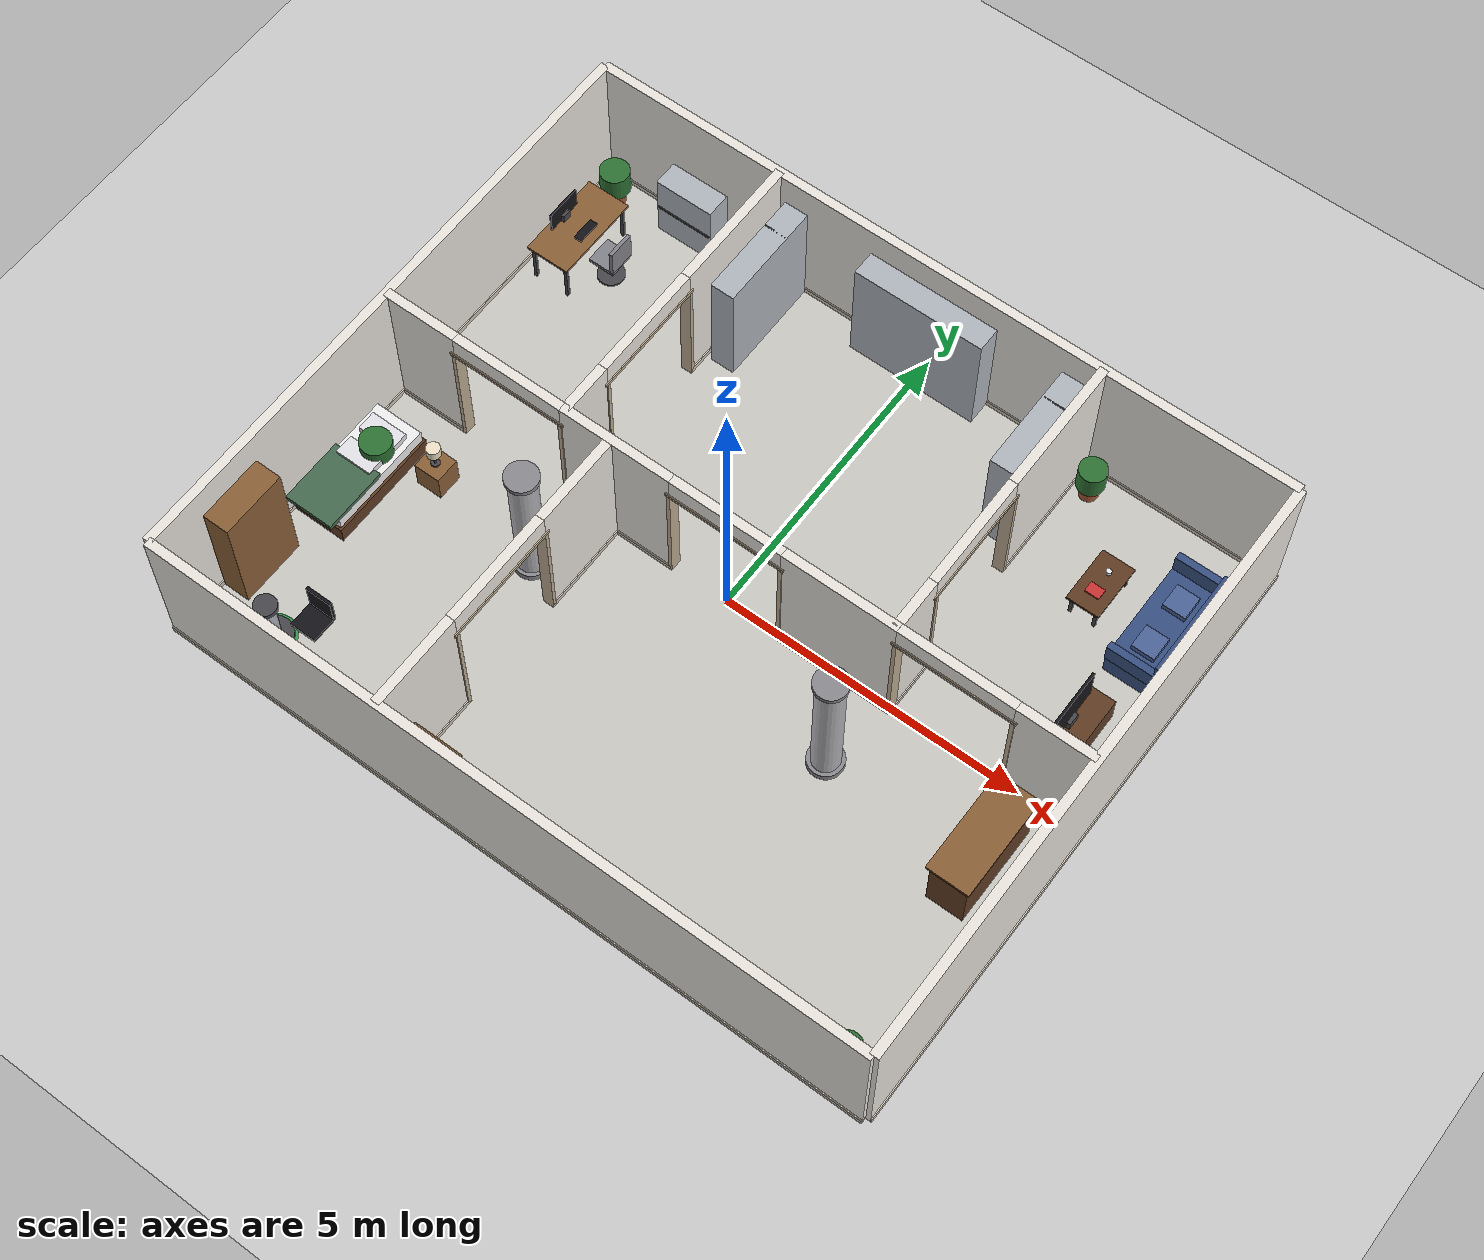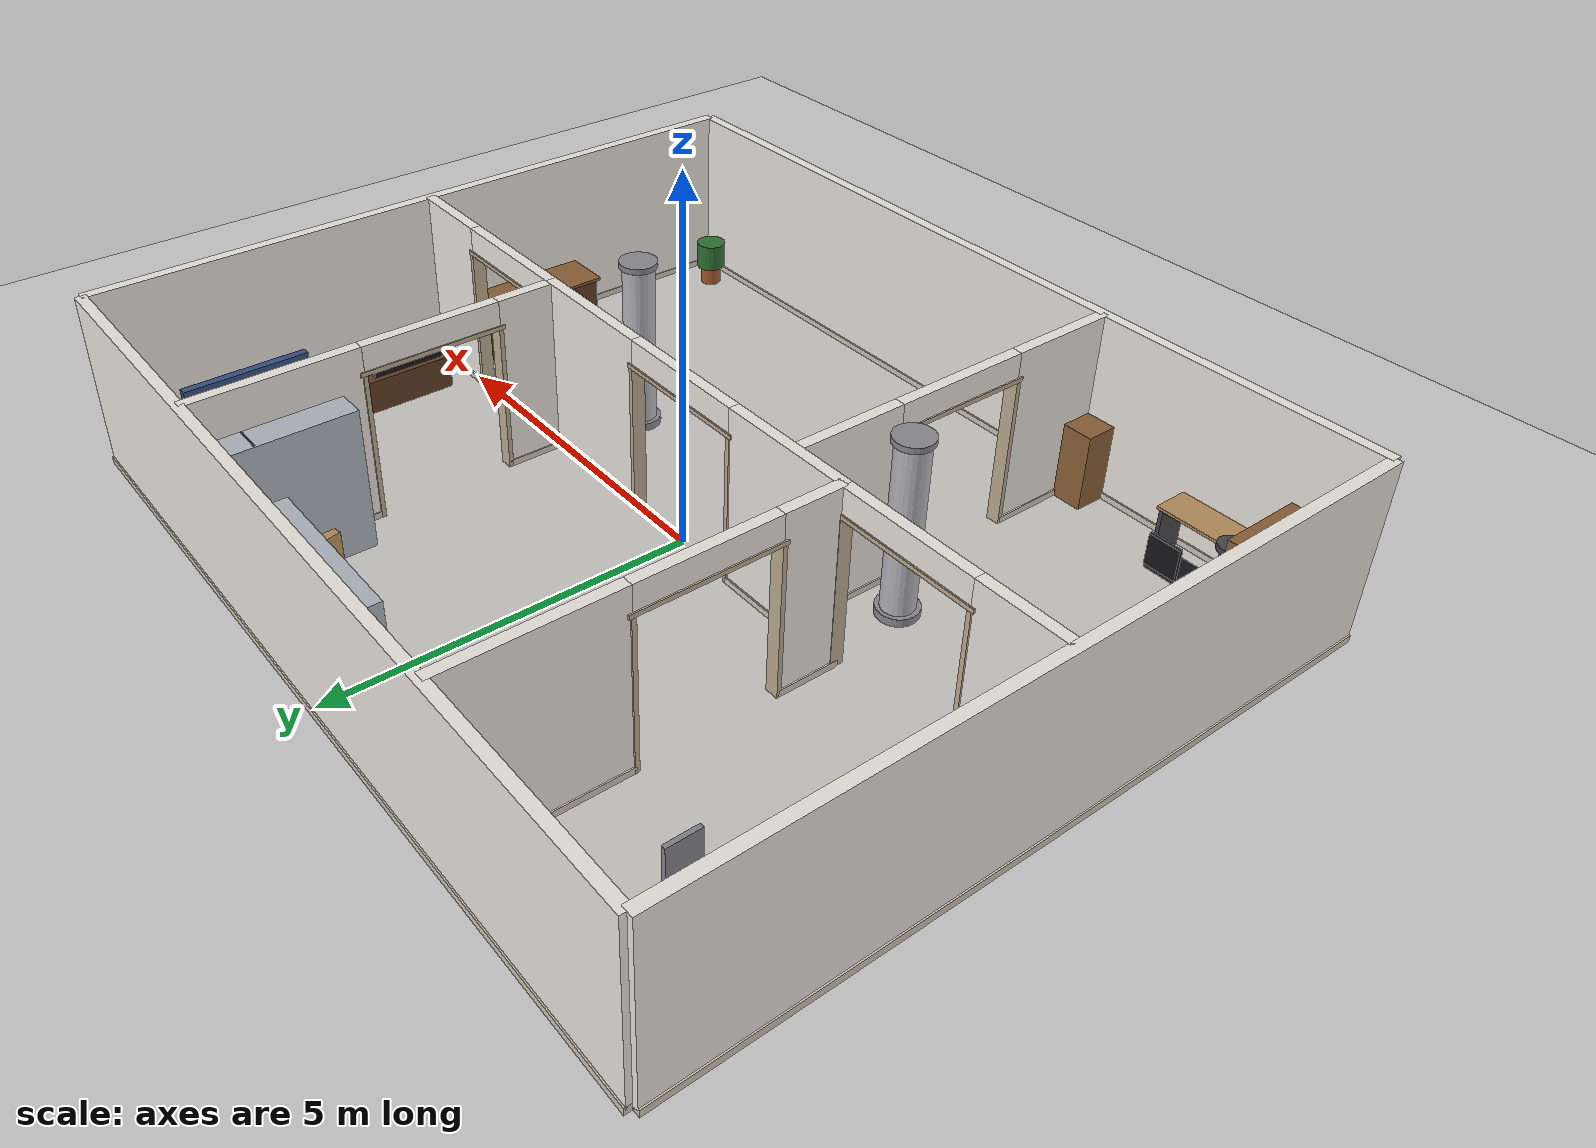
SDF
<?xml version="1.0" ?>
<sdf version="1.4">
  <world name="complex_indoor">
    <physics type="ode">
      <max_step_size>0.001</max_step_size>
      <real_time_factor>1</real_time_factor>
      <real_time_update_rate>1000</real_time_update_rate>
    </physics>

    <!-- 渲染：室内偏暗氛围 -->
    <scene>
      <ambient>0.18 0.18 0.22 1</ambient>
      <background>0.30 0.32 0.35 1</background>
      <shadows>true</shadows>
    </scene>

    <!-- 太阳光（减弱，模拟室内透过窗户的自然光） -->
    <include>
      <uri>model://sun</uri>
    </include>

    <!-- 地面 -->
    <include>
      <uri>model://ground_plane</uri>
    </include>

    <!-- 室内地砖（覆盖整个场地） -->
    <model name="floor_tile">
      <static>true</static>
      <pose>0 0 0.005 0 0 0</pose>
      <link name="link">
        <collision name="collision">
          <geometry>
            <box><size>12.0 10.0 0.01</size></box>
          </geometry>
        </collision>
        <visual name="visual">
          <geometry>
            <box><size>12.0 10.0 0.01</size></box>
          </geometry>
          <material>
            <ambient>0.80 0.79 0.77 1</ambient>
            <diffuse>0.80 0.79 0.77 1</diffuse>
            <specular>0.05 0.05 0.05 1</specular>
          </material>
        </visual>
      </link>
    </model>

    <!-- 室内点光源（暖色吊灯，适度亮度） -->
    <light name="indoor_light_center" type="point">
      <pose>0 0 2.3 0 0 0</pose>
      <diffuse>0.70 0.65 0.55 1</diffuse>
      <specular>0.15 0.15 0.15 1</specular>
      <attenuation>
        <range>10.0</range>
        <constant>0.6</constant>
        <linear>0.12</linear>
        <quadratic>0.02</quadratic>
      </attenuation>
      <cast_shadows>true</cast_shadows>
    </light>
    <light name="indoor_light_north" type="point">
      <pose>0 3.0 2.3 0 0 0</pose>
      <diffuse>0.65 0.60 0.50 1</diffuse>
      <attenuation>
        <range>7.0</range>
        <constant>0.7</constant>
        <linear>0.15</linear>
        <quadratic>0.02</quadratic>
      </attenuation>
      <cast_shadows>false</cast_shadows>
    </light>
    <light name="indoor_light_south" type="point">
      <pose>0 -3.0 2.3 0 0 0</pose>
      <diffuse>0.65 0.60 0.50 1</diffuse>
      <attenuation>
        <range>7.0</range>
        <constant>0.7</constant>
        <linear>0.15</linear>
        <quadratic>0.02</quadratic>
      </attenuation>
      <cast_shadows>false</cast_shadows>
    </light>

    <!-- ============ 外墙 ============ -->
    <model name="wall_north_0">
      <static>true</static>
      <pose>0.000 5.000 1.250 0 0 0.0000</pose>
      <link name="link">
        <collision name="collision">
          <geometry>
            <box><size>12.000 0.150 2.500</size></box>
          </geometry>
        </collision>
        <visual name="visual">
          <geometry>
            <box><size>12.000 0.150 2.500</size></box>
          </geometry>
          <material>
            <ambient>0.93 0.91 0.88 1</ambient>
            <diffuse>0.93 0.91 0.88 1</diffuse>
            <specular>0.1 0.1 0.1 1</specular>
          </material>
        </visual>
      </link>
    </model>
    <model name="wall_north_base_0">
      <static>true</static>
      <pose>0.000 5.000 0.050 0 0 0.0000</pose>
      <link name="link">
        <collision name="collision">
          <geometry>
            <box><size>12.000 0.190 0.100</size></box>
          </geometry>
        </collision>
        <visual name="visual">
          <geometry>
            <box><size>12.000 0.190 0.100</size></box>
          </geometry>
          <material>
            <ambient>0.82 0.78 0.72 1</ambient>
            <diffuse>0.82 0.78 0.72 1</diffuse>
            <specular>0.1 0.1 0.1 1</specular>
          </material>
        </visual>
      </link>
    </model>
    <model name="wall_south_0">
      <static>true</static>
      <pose>0.000 -5.000 1.250 0 0 0.0000</pose>
      <link name="link">
        <collision name="collision">
          <geometry>
            <box><size>12.000 0.150 2.500</size></box>
          </geometry>
        </collision>
        <visual name="visual">
          <geometry>
            <box><size>12.000 0.150 2.500</size></box>
          </geometry>
          <material>
            <ambient>0.93 0.91 0.88 1</ambient>
            <diffuse>0.93 0.91 0.88 1</diffuse>
            <specular>0.1 0.1 0.1 1</specular>
          </material>
        </visual>
      </link>
    </model>
    <model name="wall_south_base_0">
      <static>true</static>
      <pose>0.000 -5.000 0.050 0 0 0.0000</pose>
      <link name="link">
        <collision name="collision">
          <geometry>
            <box><size>12.000 0.190 0.100</size></box>
          </geometry>
        </collision>
        <visual name="visual">
          <geometry>
            <box><size>12.000 0.190 0.100</size></box>
          </geometry>
          <material>
            <ambient>0.82 0.78 0.72 1</ambient>
            <diffuse>0.82 0.78 0.72 1</diffuse>
            <specular>0.1 0.1 0.1 1</specular>
          </material>
        </visual>
      </link>
    </model>
    <model name="wall_east_0">
      <static>true</static>
      <pose>6.000 0.000 1.250 0 0 0.0000</pose>
      <link name="link">
        <collision name="collision">
          <geometry>
            <box><size>0.150 10.000 2.500</size></box>
          </geometry>
        </collision>
        <visual name="visual">
          <geometry>
            <box><size>0.150 10.000 2.500</size></box>
          </geometry>
          <material>
            <ambient>0.93 0.91 0.88 1</ambient>
            <diffuse>0.93 0.91 0.88 1</diffuse>
            <specular>0.1 0.1 0.1 1</specular>
          </material>
        </visual>
      </link>
    </model>
    <model name="wall_east_base_0">
      <static>true</static>
      <pose>6.000 0.000 0.050 0 0 0.0000</pose>
      <link name="link">
        <collision name="collision">
          <geometry>
            <box><size>0.190 10.000 0.100</size></box>
          </geometry>
        </collision>
        <visual name="visual">
          <geometry>
            <box><size>0.190 10.000 0.100</size></box>
          </geometry>
          <material>
            <ambient>0.82 0.78 0.72 1</ambient>
            <diffuse>0.82 0.78 0.72 1</diffuse>
            <specular>0.1 0.1 0.1 1</specular>
          </material>
        </visual>
      </link>
    </model>
    <model name="wall_west_0">
      <static>true</static>
      <pose>-6.000 0.000 1.250 0 0 0.0000</pose>
      <link name="link">
        <collision name="collision">
          <geometry>
            <box><size>0.150 10.000 2.500</size></box>
          </geometry>
        </collision>
        <visual name="visual">
          <geometry>
            <box><size>0.150 10.000 2.500</size></box>
          </geometry>
          <material>
            <ambient>0.93 0.91 0.88 1</ambient>
            <diffuse>0.93 0.91 0.88 1</diffuse>
            <specular>0.1 0.1 0.1 1</specular>
          </material>
        </visual>
      </link>
    </model>
    <model name="wall_west_base_0">
      <static>true</static>
      <pose>-6.000 0.000 0.050 0 0 0.0000</pose>
      <link name="link">
        <collision name="collision">
          <geometry>
            <box><size>0.190 10.000 0.100</size></box>
          </geometry>
        </collision>
        <visual name="visual">
          <geometry>
            <box><size>0.190 10.000 0.100</size></box>
          </geometry>
          <material>
            <ambient>0.82 0.78 0.72 1</ambient>
            <diffuse>0.82 0.78 0.72 1</diffuse>
            <specular>0.1 0.1 0.1 1</specular>
          </material>
        </visual>
      </link>
    </model>
    <!-- ============ 主分隔墙：南/北区分界 ============ -->
    <model name="wall_split_0">
      <static>true</static>
      <pose>-5.375 0.000 1.250 0 0 0.0000</pose>
      <link name="link">
        <collision name="collision">
          <geometry>
            <box><size>1.250 0.150 2.500</size></box>
          </geometry>
        </collision>
        <visual name="visual">
          <geometry>
            <box><size>1.250 0.150 2.500</size></box>
          </geometry>
          <material>
            <ambient>0.93 0.91 0.88 1</ambient>
            <diffuse>0.93 0.91 0.88 1</diffuse>
            <specular>0.1 0.1 0.1 1</specular>
          </material>
        </visual>
      </link>
    </model>
    <model name="wall_split_base_0">
      <static>true</static>
      <pose>-5.375 0.000 0.050 0 0 0.0000</pose>
      <link name="link">
        <collision name="collision">
          <geometry>
            <box><size>1.250 0.190 0.100</size></box>
          </geometry>
        </collision>
        <visual name="visual">
          <geometry>
            <box><size>1.250 0.190 0.100</size></box>
          </geometry>
          <material>
            <ambient>0.82 0.78 0.72 1</ambient>
            <diffuse>0.82 0.78 0.72 1</diffuse>
            <specular>0.1 0.1 0.1 1</specular>
          </material>
        </visual>
      </link>
    </model>
    <model name="wall_split_lintel_1">
      <static>true</static>
      <pose>-3.800 0.000 2.300 0 0 0.0000</pose>
      <link name="link">
        <collision name="collision">
          <geometry>
            <box><size>1.900 0.150 0.400</size></box>
          </geometry>
        </collision>
        <visual name="visual">
          <geometry>
            <box><size>1.900 0.150 0.400</size></box>
          </geometry>
          <material>
            <ambient>0.93 0.91 0.88 1</ambient>
            <diffuse>0.93 0.91 0.88 1</diffuse>
            <specular>0.1 0.1 0.1 1</specular>
          </material>
        </visual>
      </link>
    </model>
    <model name="wall_split_frame_1_l">
      <static>true</static>
      <pose>-4.750 0.000 1.050 0 0 0.0000</pose>
      <link name="link">
        <collision name="collision">
          <geometry>
            <box><size>0.060 0.190 2.100</size></box>
          </geometry>
        </collision>
        <visual name="visual">
          <geometry>
            <box><size>0.060 0.190 2.100</size></box>
          </geometry>
          <material>
            <ambient>0.75 0.68 0.58 1</ambient>
            <diffuse>0.75 0.68 0.58 1</diffuse>
            <specular>0.1 0.1 0.1 1</specular>
          </material>
        </visual>
      </link>
    </model>
    <model name="wall_split_frame_1_r">
      <static>true</static>
      <pose>-2.850 0.000 1.050 0 0 0.0000</pose>
      <link name="link">
        <collision name="collision">
          <geometry>
            <box><size>0.060 0.190 2.100</size></box>
          </geometry>
        </collision>
        <visual name="visual">
          <geometry>
            <box><size>0.060 0.190 2.100</size></box>
          </geometry>
          <material>
            <ambient>0.75 0.68 0.58 1</ambient>
            <diffuse>0.75 0.68 0.58 1</diffuse>
            <specular>0.1 0.1 0.1 1</specular>
          </material>
        </visual>
      </link>
    </model>
    <model name="wall_split_frame_1_t">
      <static>true</static>
      <pose>-3.800 0.000 2.130 0 0 0.0000</pose>
      <link name="link">
        <collision name="collision">
          <geometry>
            <box><size>2.020 0.190 0.060</size></box>
          </geometry>
        </collision>
        <visual name="visual">
          <geometry>
            <box><size>2.020 0.190 0.060</size></box>
          </geometry>
          <material>
            <ambient>0.75 0.68 0.58 1</ambient>
            <diffuse>0.75 0.68 0.58 1</diffuse>
            <specular>0.1 0.1 0.1 1</specular>
          </material>
        </visual>
      </link>
    </model>
    <model name="wall_split_2">
      <static>true</static>
      <pose>-1.900 0.000 1.250 0 0 0.0000</pose>
      <link name="link">
        <collision name="collision">
          <geometry>
            <box><size>1.900 0.150 2.500</size></box>
          </geometry>
        </collision>
        <visual name="visual">
          <geometry>
            <box><size>1.900 0.150 2.500</size></box>
          </geometry>
          <material>
            <ambient>0.93 0.91 0.88 1</ambient>
            <diffuse>0.93 0.91 0.88 1</diffuse>
            <specular>0.1 0.1 0.1 1</specular>
          </material>
        </visual>
      </link>
    </model>
    <model name="wall_split_base_2">
      <static>true</static>
      <pose>-1.900 0.000 0.050 0 0 0.0000</pose>
      <link name="link">
        <collision name="collision">
          <geometry>
            <box><size>1.900 0.190 0.100</size></box>
          </geometry>
        </collision>
        <visual name="visual">
          <geometry>
            <box><size>1.900 0.190 0.100</size></box>
          </geometry>
          <material>
            <ambient>0.82 0.78 0.72 1</ambient>
            <diffuse>0.82 0.78 0.72 1</diffuse>
            <specular>0.1 0.1 0.1 1</specular>
          </material>
        </visual>
      </link>
    </model>
    <model name="wall_split_lintel_3">
      <static>true</static>
      <pose>0.000 0.000 2.300 0 0 0.0000</pose>
      <link name="link">
        <collision name="collision">
          <geometry>
            <box><size>1.900 0.150 0.400</size></box>
          </geometry>
        </collision>
        <visual name="visual">
          <geometry>
            <box><size>1.900 0.150 0.400</size></box>
          </geometry>
          <material>
            <ambient>0.93 0.91 0.88 1</ambient>
            <diffuse>0.93 0.91 0.88 1</diffuse>
            <specular>0.1 0.1 0.1 1</specular>
          </material>
        </visual>
      </link>
    </model>
    <model name="wall_split_frame_3_l">
      <static>true</static>
      <pose>-0.950 0.000 1.050 0 0 0.0000</pose>
      <link name="link">
        <collision name="collision">
          <geometry>
            <box><size>0.060 0.190 2.100</size></box>
          </geometry>
        </collision>
        <visual name="visual">
          <geometry>
            <box><size>0.060 0.190 2.100</size></box>
          </geometry>
          <material>
            <ambient>0.75 0.68 0.58 1</ambient>
            <diffuse>0.75 0.68 0.58 1</diffuse>
            <specular>0.1 0.1 0.1 1</specular>
          </material>
        </visual>
      </link>
    </model>
    <model name="wall_split_frame_3_r">
      <static>true</static>
      <pose>0.950 0.000 1.050 0 0 0.0000</pose>
      <link name="link">
        <collision name="collision">
          <geometry>
            <box><size>0.060 0.190 2.100</size></box>
          </geometry>
        </collision>
        <visual name="visual">
          <geometry>
            <box><size>0.060 0.190 2.100</size></box>
          </geometry>
          <material>
            <ambient>0.75 0.68 0.58 1</ambient>
            <diffuse>0.75 0.68 0.58 1</diffuse>
            <specular>0.1 0.1 0.1 1</specular>
          </material>
        </visual>
      </link>
    </model>
    <model name="wall_split_frame_3_t">
      <static>true</static>
      <pose>0.000 0.000 2.130 0 0 0.0000</pose>
      <link name="link">
        <collision name="collision">
          <geometry>
            <box><size>2.020 0.190 0.060</size></box>
          </geometry>
        </collision>
        <visual name="visual">
          <geometry>
            <box><size>2.020 0.190 0.060</size></box>
          </geometry>
          <material>
            <ambient>0.75 0.68 0.58 1</ambient>
            <diffuse>0.75 0.68 0.58 1</diffuse>
            <specular>0.1 0.1 0.1 1</specular>
          </material>
        </visual>
      </link>
    </model>
    <model name="wall_split_4">
      <static>true</static>
      <pose>1.900 0.000 1.250 0 0 0.0000</pose>
      <link name="link">
        <collision name="collision">
          <geometry>
            <box><size>1.900 0.150 2.500</size></box>
          </geometry>
        </collision>
        <visual name="visual">
          <geometry>
            <box><size>1.900 0.150 2.500</size></box>
          </geometry>
          <material>
            <ambient>0.93 0.91 0.88 1</ambient>
            <diffuse>0.93 0.91 0.88 1</diffuse>
            <specular>0.1 0.1 0.1 1</specular>
          </material>
        </visual>
      </link>
    </model>
    <model name="wall_split_base_4">
      <static>true</static>
      <pose>1.900 0.000 0.050 0 0 0.0000</pose>
      <link name="link">
        <collision name="collision">
          <geometry>
            <box><size>1.900 0.190 0.100</size></box>
          </geometry>
        </collision>
        <visual name="visual">
          <geometry>
            <box><size>1.900 0.190 0.100</size></box>
          </geometry>
          <material>
            <ambient>0.82 0.78 0.72 1</ambient>
            <diffuse>0.82 0.78 0.72 1</diffuse>
            <specular>0.1 0.1 0.1 1</specular>
          </material>
        </visual>
      </link>
    </model>
    <model name="wall_split_lintel_5">
      <static>true</static>
      <pose>3.800 0.000 2.300 0 0 0.0000</pose>
      <link name="link">
        <collision name="collision">
          <geometry>
            <box><size>1.900 0.150 0.400</size></box>
          </geometry>
        </collision>
        <visual name="visual">
          <geometry>
            <box><size>1.900 0.150 0.400</size></box>
          </geometry>
          <material>
            <ambient>0.93 0.91 0.88 1</ambient>
            <diffuse>0.93 0.91 0.88 1</diffuse>
            <specular>0.1 0.1 0.1 1</specular>
          </material>
        </visual>
      </link>
    </model>
    <model name="wall_split_frame_5_l">
      <static>true</static>
      <pose>2.850 0.000 1.050 0 0 0.0000</pose>
      <link name="link">
        <collision name="collision">
          <geometry>
            <box><size>0.060 0.190 2.100</size></box>
          </geometry>
        </collision>
        <visual name="visual">
          <geometry>
            <box><size>0.060 0.190 2.100</size></box>
          </geometry>
          <material>
            <ambient>0.75 0.68 0.58 1</ambient>
            <diffuse>0.75 0.68 0.58 1</diffuse>
            <specular>0.1 0.1 0.1 1</specular>
          </material>
        </visual>
      </link>
    </model>
    <model name="wall_split_frame_5_r">
      <static>true</static>
      <pose>4.750 0.000 1.050 0 0 0.0000</pose>
      <link name="link">
        <collision name="collision">
          <geometry>
            <box><size>0.060 0.190 2.100</size></box>
          </geometry>
        </collision>
        <visual name="visual">
          <geometry>
            <box><size>0.060 0.190 2.100</size></box>
          </geometry>
          <material>
            <ambient>0.75 0.68 0.58 1</ambient>
            <diffuse>0.75 0.68 0.58 1</diffuse>
            <specular>0.1 0.1 0.1 1</specular>
          </material>
        </visual>
      </link>
    </model>
    <model name="wall_split_frame_5_t">
      <static>true</static>
      <pose>3.800 0.000 2.130 0 0 0.0000</pose>
      <link name="link">
        <collision name="collision">
          <geometry>
            <box><size>2.020 0.190 0.060</size></box>
          </geometry>
        </collision>
        <visual name="visual">
          <geometry>
            <box><size>2.020 0.190 0.060</size></box>
          </geometry>
          <material>
            <ambient>0.75 0.68 0.58 1</ambient>
            <diffuse>0.75 0.68 0.58 1</diffuse>
            <specular>0.1 0.1 0.1 1</specular>
          </material>
        </visual>
      </link>
    </model>
    <model name="wall_split_6">
      <static>true</static>
      <pose>5.375 0.000 1.250 0 0 0.0000</pose>
      <link name="link">
        <collision name="collision">
          <geometry>
            <box><size>1.250 0.150 2.500</size></box>
          </geometry>
        </collision>
        <visual name="visual">
          <geometry>
            <box><size>1.250 0.150 2.500</size></box>
          </geometry>
          <material>
            <ambient>0.93 0.91 0.88 1</ambient>
            <diffuse>0.93 0.91 0.88 1</diffuse>
            <specular>0.1 0.1 0.1 1</specular>
          </material>
        </visual>
      </link>
    </model>
    <model name="wall_split_base_6">
      <static>true</static>
      <pose>5.375 0.000 0.050 0 0 0.0000</pose>
      <link name="link">
        <collision name="collision">
          <geometry>
            <box><size>1.250 0.190 0.100</size></box>
          </geometry>
        </collision>
        <visual name="visual">
          <geometry>
            <box><size>1.250 0.190 0.100</size></box>
          </geometry>
          <material>
            <ambient>0.82 0.78 0.72 1</ambient>
            <diffuse>0.82 0.78 0.72 1</diffuse>
            <specular>0.1 0.1 0.1 1</specular>
          </material>
        </visual>
      </link>
    </model>
    <!-- ============ 北区隔墙 ============ -->
    <model name="wall_north_div1_0">
      <static>true</static>
      <pose>-2.800 0.425 1.250 0 0 0.0000</pose>
      <link name="link">
        <collision name="collision">
          <geometry>
            <box><size>0.150 0.850 2.500</size></box>
          </geometry>
        </collision>
        <visual name="visual">
          <geometry>
            <box><size>0.150 0.850 2.500</size></box>
          </geometry>
          <material>
            <ambient>0.93 0.91 0.88 1</ambient>
            <diffuse>0.93 0.91 0.88 1</diffuse>
            <specular>0.1 0.1 0.1 1</specular>
          </material>
        </visual>
      </link>
    </model>
    <model name="wall_north_div1_base_0">
      <static>true</static>
      <pose>-2.800 0.425 0.050 0 0 0.0000</pose>
      <link name="link">
        <collision name="collision">
          <geometry>
            <box><size>0.190 0.850 0.100</size></box>
          </geometry>
        </collision>
        <visual name="visual">
          <geometry>
            <box><size>0.190 0.850 0.100</size></box>
          </geometry>
          <material>
            <ambient>0.82 0.78 0.72 1</ambient>
            <diffuse>0.82 0.78 0.72 1</diffuse>
            <specular>0.1 0.1 0.1 1</specular>
          </material>
        </visual>
      </link>
    </model>
    <model name="wall_north_div1_lintel_1">
      <static>true</static>
      <pose>-2.800 1.800 2.300 0 0 0.0000</pose>
      <link name="link">
        <collision name="collision">
          <geometry>
            <box><size>0.150 1.900 0.400</size></box>
          </geometry>
        </collision>
        <visual name="visual">
          <geometry>
            <box><size>0.150 1.900 0.400</size></box>
          </geometry>
          <material>
            <ambient>0.93 0.91 0.88 1</ambient>
            <diffuse>0.93 0.91 0.88 1</diffuse>
            <specular>0.1 0.1 0.1 1</specular>
          </material>
        </visual>
      </link>
    </model>
    <model name="wall_north_div1_frame_1_b">
      <static>true</static>
      <pose>-2.800 0.850 1.050 0 0 0.0000</pose>
      <link name="link">
        <collision name="collision">
          <geometry>
            <box><size>0.190 0.060 2.100</size></box>
          </geometry>
        </collision>
        <visual name="visual">
          <geometry>
            <box><size>0.190 0.060 2.100</size></box>
          </geometry>
          <material>
            <ambient>0.75 0.68 0.58 1</ambient>
            <diffuse>0.75 0.68 0.58 1</diffuse>
            <specular>0.1 0.1 0.1 1</specular>
          </material>
        </visual>
      </link>
    </model>
    <model name="wall_north_div1_frame_1_t">
      <static>true</static>
      <pose>-2.800 2.750 1.050 0 0 0.0000</pose>
      <link name="link">
        <collision name="collision">
          <geometry>
            <box><size>0.190 0.060 2.100</size></box>
          </geometry>
        </collision>
        <visual name="visual">
          <geometry>
            <box><size>0.190 0.060 2.100</size></box>
          </geometry>
          <material>
            <ambient>0.75 0.68 0.58 1</ambient>
            <diffuse>0.75 0.68 0.58 1</diffuse>
            <specular>0.1 0.1 0.1 1</specular>
          </material>
        </visual>
      </link>
    </model>
    <model name="wall_north_div1_frame_1_top">
      <static>true</static>
      <pose>-2.800 1.800 2.130 0 0 0.0000</pose>
      <link name="link">
        <collision name="collision">
          <geometry>
            <box><size>0.190 2.020 0.060</size></box>
          </geometry>
        </collision>
        <visual name="visual">
          <geometry>
            <box><size>0.190 2.020 0.060</size></box>
          </geometry>
          <material>
            <ambient>0.75 0.68 0.58 1</ambient>
            <diffuse>0.75 0.68 0.58 1</diffuse>
            <specular>0.1 0.1 0.1 1</specular>
          </material>
        </visual>
      </link>
    </model>
    <model name="wall_north_div1_2">
      <static>true</static>
      <pose>-2.800 3.875 1.250 0 0 0.0000</pose>
      <link name="link">
        <collision name="collision">
          <geometry>
            <box><size>0.150 2.250 2.500</size></box>
          </geometry>
        </collision>
        <visual name="visual">
          <geometry>
            <box><size>0.150 2.250 2.500</size></box>
          </geometry>
          <material>
            <ambient>0.93 0.91 0.88 1</ambient>
            <diffuse>0.93 0.91 0.88 1</diffuse>
            <specular>0.1 0.1 0.1 1</specular>
          </material>
        </visual>
      </link>
    </model>
    <model name="wall_north_div1_base_2">
      <static>true</static>
      <pose>-2.800 3.875 0.050 0 0 0.0000</pose>
      <link name="link">
        <collision name="collision">
          <geometry>
            <box><size>0.190 2.250 0.100</size></box>
          </geometry>
        </collision>
        <visual name="visual">
          <geometry>
            <box><size>0.190 2.250 0.100</size></box>
          </geometry>
          <material>
            <ambient>0.82 0.78 0.72 1</ambient>
            <diffuse>0.82 0.78 0.72 1</diffuse>
            <specular>0.1 0.1 0.1 1</specular>
          </material>
        </visual>
      </link>
    </model>
    <model name="wall_north_div2_0">
      <static>true</static>
      <pose>2.800 0.425 1.250 0 0 0.0000</pose>
      <link name="link">
        <collision name="collision">
          <geometry>
            <box><size>0.150 0.850 2.500</size></box>
          </geometry>
        </collision>
        <visual name="visual">
          <geometry>
            <box><size>0.150 0.850 2.500</size></box>
          </geometry>
          <material>
            <ambient>0.93 0.91 0.88 1</ambient>
            <diffuse>0.93 0.91 0.88 1</diffuse>
            <specular>0.1 0.1 0.1 1</specular>
          </material>
        </visual>
      </link>
    </model>
    <model name="wall_north_div2_base_0">
      <static>true</static>
      <pose>2.800 0.425 0.050 0 0 0.0000</pose>
      <link name="link">
        <collision name="collision">
          <geometry>
            <box><size>0.190 0.850 0.100</size></box>
          </geometry>
        </collision>
        <visual name="visual">
          <geometry>
            <box><size>0.190 0.850 0.100</size></box>
          </geometry>
          <material>
            <ambient>0.82 0.78 0.72 1</ambient>
            <diffuse>0.82 0.78 0.72 1</diffuse>
            <specular>0.1 0.1 0.1 1</specular>
          </material>
        </visual>
      </link>
    </model>
    <model name="wall_north_div2_lintel_1">
      <static>true</static>
      <pose>2.800 1.800 2.300 0 0 0.0000</pose>
      <link name="link">
        <collision name="collision">
          <geometry>
            <box><size>0.150 1.900 0.400</size></box>
          </geometry>
        </collision>
        <visual name="visual">
          <geometry>
            <box><size>0.150 1.900 0.400</size></box>
          </geometry>
          <material>
            <ambient>0.93 0.91 0.88 1</ambient>
            <diffuse>0.93 0.91 0.88 1</diffuse>
            <specular>0.1 0.1 0.1 1</specular>
          </material>
        </visual>
      </link>
    </model>
    <model name="wall_north_div2_frame_1_b">
      <static>true</static>
      <pose>2.800 0.850 1.050 0 0 0.0000</pose>
      <link name="link">
        <collision name="collision">
          <geometry>
            <box><size>0.190 0.060 2.100</size></box>
          </geometry>
        </collision>
        <visual name="visual">
          <geometry>
            <box><size>0.190 0.060 2.100</size></box>
          </geometry>
          <material>
            <ambient>0.75 0.68 0.58 1</ambient>
            <diffuse>0.75 0.68 0.58 1</diffuse>
            <specular>0.1 0.1 0.1 1</specular>
          </material>
        </visual>
      </link>
    </model>
    <model name="wall_north_div2_frame_1_t">
      <static>true</static>
      <pose>2.800 2.750 1.050 0 0 0.0000</pose>
      <link name="link">
        <collision name="collision">
          <geometry>
            <box><size>0.190 0.060 2.100</size></box>
          </geometry>
        </collision>
        <visual name="visual">
          <geometry>
            <box><size>0.190 0.060 2.100</size></box>
          </geometry>
          <material>
            <ambient>0.75 0.68 0.58 1</ambient>
            <diffuse>0.75 0.68 0.58 1</diffuse>
            <specular>0.1 0.1 0.1 1</specular>
          </material>
        </visual>
      </link>
    </model>
    <model name="wall_north_div2_frame_1_top">
      <static>true</static>
      <pose>2.800 1.800 2.130 0 0 0.0000</pose>
      <link name="link">
        <collision name="collision">
          <geometry>
            <box><size>0.190 2.020 0.060</size></box>
          </geometry>
        </collision>
        <visual name="visual">
          <geometry>
            <box><size>0.190 2.020 0.060</size></box>
          </geometry>
          <material>
            <ambient>0.75 0.68 0.58 1</ambient>
            <diffuse>0.75 0.68 0.58 1</diffuse>
            <specular>0.1 0.1 0.1 1</specular>
          </material>
        </visual>
      </link>
    </model>
    <model name="wall_north_div2_2">
      <static>true</static>
      <pose>2.800 3.875 1.250 0 0 0.0000</pose>
      <link name="link">
        <collision name="collision">
          <geometry>
            <box><size>0.150 2.250 2.500</size></box>
          </geometry>
        </collision>
        <visual name="visual">
          <geometry>
            <box><size>0.150 2.250 2.500</size></box>
          </geometry>
          <material>
            <ambient>0.93 0.91 0.88 1</ambient>
            <diffuse>0.93 0.91 0.88 1</diffuse>
            <specular>0.1 0.1 0.1 1</specular>
          </material>
        </visual>
      </link>
    </model>
    <model name="wall_north_div2_base_2">
      <static>true</static>
      <pose>2.800 3.875 0.050 0 0 0.0000</pose>
      <link name="link">
        <collision name="collision">
          <geometry>
            <box><size>0.190 2.250 0.100</size></box>
          </geometry>
        </collision>
        <visual name="visual">
          <geometry>
            <box><size>0.190 2.250 0.100</size></box>
          </geometry>
          <material>
            <ambient>0.82 0.78 0.72 1</ambient>
            <diffuse>0.82 0.78 0.72 1</diffuse>
            <specular>0.1 0.1 0.1 1</specular>
          </material>
        </visual>
      </link>
    </model>
    <!-- ============ 南区隔墙 ============ -->
    <model name="wall_south_div_0">
      <static>true</static>
      <pose>-2.000 -4.225 1.250 0 0 0.0000</pose>
      <link name="link">
        <collision name="collision">
          <geometry>
            <box><size>0.150 1.550 2.500</size></box>
          </geometry>
        </collision>
        <visual name="visual">
          <geometry>
            <box><size>0.150 1.550 2.500</size></box>
          </geometry>
          <material>
            <ambient>0.93 0.91 0.88 1</ambient>
            <diffuse>0.93 0.91 0.88 1</diffuse>
            <specular>0.1 0.1 0.1 1</specular>
          </material>
        </visual>
      </link>
    </model>
    <model name="wall_south_div_base_0">
      <static>true</static>
      <pose>-2.000 -4.225 0.050 0 0 0.0000</pose>
      <link name="link">
        <collision name="collision">
          <geometry>
            <box><size>0.190 1.550 0.100</size></box>
          </geometry>
        </collision>
        <visual name="visual">
          <geometry>
            <box><size>0.190 1.550 0.100</size></box>
          </geometry>
          <material>
            <ambient>0.82 0.78 0.72 1</ambient>
            <diffuse>0.82 0.78 0.72 1</diffuse>
            <specular>0.1 0.1 0.1 1</specular>
          </material>
        </visual>
      </link>
    </model>
    <model name="wall_south_div_lintel_1">
      <static>true</static>
      <pose>-2.000 -2.500 2.300 0 0 0.0000</pose>
      <link name="link">
        <collision name="collision">
          <geometry>
            <box><size>0.150 1.900 0.400</size></box>
          </geometry>
        </collision>
        <visual name="visual">
          <geometry>
            <box><size>0.150 1.900 0.400</size></box>
          </geometry>
          <material>
            <ambient>0.93 0.91 0.88 1</ambient>
            <diffuse>0.93 0.91 0.88 1</diffuse>
            <specular>0.1 0.1 0.1 1</specular>
          </material>
        </visual>
      </link>
    </model>
    <model name="wall_south_div_frame_1_b">
      <static>true</static>
      <pose>-2.000 -3.450 1.050 0 0 0.0000</pose>
      <link name="link">
        <collision name="collision">
          <geometry>
            <box><size>0.190 0.060 2.100</size></box>
          </geometry>
        </collision>
        <visual name="visual">
          <geometry>
            <box><size>0.190 0.060 2.100</size></box>
          </geometry>
          <material>
            <ambient>0.75 0.68 0.58 1</ambient>
            <diffuse>0.75 0.68 0.58 1</diffuse>
            <specular>0.1 0.1 0.1 1</specular>
          </material>
        </visual>
      </link>
    </model>
    <model name="wall_south_div_frame_1_t">
      <static>true</static>
      <pose>-2.000 -1.550 1.050 0 0 0.0000</pose>
      <link name="link">
        <collision name="collision">
          <geometry>
            <box><size>0.190 0.060 2.100</size></box>
          </geometry>
        </collision>
        <visual name="visual">
          <geometry>
            <box><size>0.190 0.060 2.100</size></box>
          </geometry>
          <material>
            <ambient>0.75 0.68 0.58 1</ambient>
            <diffuse>0.75 0.68 0.58 1</diffuse>
            <specular>0.1 0.1 0.1 1</specular>
          </material>
        </visual>
      </link>
    </model>
    <model name="wall_south_div_frame_1_top">
      <static>true</static>
      <pose>-2.000 -2.500 2.130 0 0 0.0000</pose>
      <link name="link">
        <collision name="collision">
          <geometry>
            <box><size>0.190 2.020 0.060</size></box>
          </geometry>
        </collision>
        <visual name="visual">
          <geometry>
            <box><size>0.190 2.020 0.060</size></box>
          </geometry>
          <material>
            <ambient>0.75 0.68 0.58 1</ambient>
            <diffuse>0.75 0.68 0.58 1</diffuse>
            <specular>0.1 0.1 0.1 1</specular>
          </material>
        </visual>
      </link>
    </model>
    <model name="wall_south_div_2">
      <static>true</static>
      <pose>-2.000 -0.775 1.250 0 0 0.0000</pose>
      <link name="link">
        <collision name="collision">
          <geometry>
            <box><size>0.150 1.550 2.500</size></box>
          </geometry>
        </collision>
        <visual name="visual">
          <geometry>
            <box><size>0.150 1.550 2.500</size></box>
          </geometry>
          <material>
            <ambient>0.93 0.91 0.88 1</ambient>
            <diffuse>0.93 0.91 0.88 1</diffuse>
            <specular>0.1 0.1 0.1 1</specular>
          </material>
        </visual>
      </link>
    </model>
    <model name="wall_south_div_base_2">
      <static>true</static>
      <pose>-2.000 -0.775 0.050 0 0 0.0000</pose>
      <link name="link">
        <collision name="collision">
          <geometry>
            <box><size>0.190 1.550 0.100</size></box>
          </geometry>
        </collision>
        <visual name="visual">
          <geometry>
            <box><size>0.190 1.550 0.100</size></box>
          </geometry>
          <material>
            <ambient>0.82 0.78 0.72 1</ambient>
            <diffuse>0.82 0.78 0.72 1</diffuse>
            <specular>0.1 0.1 0.1 1</specular>
          </material>
        </visual>
      </link>
    </model>
    <!-- ============ 家具与装饰（一律贴墙） ============ -->
    <model name="desk_a_top">
      <static>true</static>
      <pose>-5.350 3.400 0.740 0 0 0.0000</pose>
      <link name="link">
        <collision name="collision">
          <geometry>
            <box><size>0.750 1.500 0.040</size></box>
          </geometry>
        </collision>
        <visual name="visual">
          <geometry>
            <box><size>0.750 1.500 0.040</size></box>
          </geometry>
          <material>
            <ambient>0.55 0.38 0.22 1</ambient>
            <diffuse>0.55 0.38 0.22 1</diffuse>
            <specular>0.1 0.1 0.1 1</specular>
          </material>
        </visual>
      </link>
    </model>
    <model name="desk_a_leg_1">
      <static>true</static>
      <pose>-5.650 2.720 0.360 0 0 0.0000</pose>
      <link name="link">
        <collision name="collision">
          <geometry>
            <box><size>0.050 0.050 0.720</size></box>
          </geometry>
        </collision>
        <visual name="visual">
          <geometry>
            <box><size>0.050 0.050 0.720</size></box>
          </geometry>
          <material>
            <ambient>0.28 0.28 0.30 1</ambient>
            <diffuse>0.28 0.28 0.30 1</diffuse>
            <specular>0.1 0.1 0.1 1</specular>
          </material>
        </visual>
      </link>
    </model>
    <model name="desk_a_leg_2">
      <static>true</static>
      <pose>-5.050 2.720 0.360 0 0 0.0000</pose>
      <link name="link">
        <collision name="collision">
          <geometry>
            <box><size>0.050 0.050 0.720</size></box>
          </geometry>
        </collision>
        <visual name="visual">
          <geometry>
            <box><size>0.050 0.050 0.720</size></box>
          </geometry>
          <material>
            <ambient>0.28 0.28 0.30 1</ambient>
            <diffuse>0.28 0.28 0.30 1</diffuse>
            <specular>0.1 0.1 0.1 1</specular>
          </material>
        </visual>
      </link>
    </model>
    <model name="desk_a_leg_3">
      <static>true</static>
      <pose>-5.650 4.080 0.360 0 0 0.0000</pose>
      <link name="link">
        <collision name="collision">
          <geometry>
            <box><size>0.050 0.050 0.720</size></box>
          </geometry>
        </collision>
        <visual name="visual">
          <geometry>
            <box><size>0.050 0.050 0.720</size></box>
          </geometry>
          <material>
            <ambient>0.28 0.28 0.30 1</ambient>
            <diffuse>0.28 0.28 0.30 1</diffuse>
            <specular>0.1 0.1 0.1 1</specular>
          </material>
        </visual>
      </link>
    </model>
    <model name="desk_a_leg_4">
      <static>true</static>
      <pose>-5.050 4.080 0.360 0 0 0.0000</pose>
      <link name="link">
        <collision name="collision">
          <geometry>
            <box><size>0.050 0.050 0.720</size></box>
          </geometry>
        </collision>
        <visual name="visual">
          <geometry>
            <box><size>0.050 0.050 0.720</size></box>
          </geometry>
          <material>
            <ambient>0.28 0.28 0.30 1</ambient>
            <diffuse>0.28 0.28 0.30 1</diffuse>
            <specular>0.1 0.1 0.1 1</specular>
          </material>
        </visual>
      </link>
    </model>
    <model name="monitor_a_screen">
      <static>true</static>
      <pose>-5.620 3.400 0.950 0 0 0.0000</pose>
      <link name="link">
        <collision name="collision">
          <geometry>
            <box><size>0.030 0.600 0.360</size></box>
          </geometry>
        </collision>
        <visual name="visual">
          <geometry>
            <box><size>0.030 0.600 0.360</size></box>
          </geometry>
          <material>
            <ambient>0.08 0.08 0.10 1</ambient>
            <diffuse>0.08 0.08 0.10 1</diffuse>
            <specular>0.1 0.1 0.1 1</specular>
          </material>
        </visual>
      </link>
    </model>
    <model name="monitor_a_stand">
      <static>true</static>
      <pose>-5.600 3.400 0.820 0 0 0.0000</pose>
      <link name="link">
        <collision name="collision">
          <geometry>
            <box><size>0.100 0.140 0.160</size></box>
          </geometry>
        </collision>
        <visual name="visual">
          <geometry>
            <box><size>0.100 0.140 0.160</size></box>
          </geometry>
          <material>
            <ambient>0.28 0.28 0.30 1</ambient>
            <diffuse>0.28 0.28 0.30 1</diffuse>
            <specular>0.1 0.1 0.1 1</specular>
          </material>
        </visual>
      </link>
    </model>
    <model name="keyboard_a">
      <static>true</static>
      <pose>-5.200 3.400 0.770 0 0 0.0000</pose>
      <link name="link">
        <collision name="collision">
          <geometry>
            <box><size>0.140 0.400 0.020</size></box>
          </geometry>
        </collision>
        <visual name="visual">
          <geometry>
            <box><size>0.140 0.400 0.020</size></box>
          </geometry>
          <material>
            <ambient>0.08 0.08 0.10 1</ambient>
            <diffuse>0.08 0.08 0.10 1</diffuse>
            <specular>0.1 0.1 0.1 1</specular>
          </material>
        </visual>
      </link>
    </model>
    <model name="chair_a_seat">
      <static>true</static>
      <pose>-4.750 3.400 0.460 0 0 0.0000</pose>
      <link name="link">
        <collision name="collision">
          <geometry>
            <box><size>0.450 0.450 0.060</size></box>
          </geometry>
        </collision>
        <visual name="visual">
          <geometry>
            <box><size>0.450 0.450 0.060</size></box>
          </geometry>
          <material>
            <ambient>0.52 0.52 0.55 1</ambient>
            <diffuse>0.52 0.52 0.55 1</diffuse>
            <specular>0.1 0.1 0.1 1</specular>
          </material>
        </visual>
      </link>
    </model>
    <model name="chair_a_back">
      <static>true</static>
      <pose>-4.550 3.400 0.720 0 0 0.0000</pose>
      <link name="link">
        <collision name="collision">
          <geometry>
            <box><size>0.060 0.450 0.480</size></box>
          </geometry>
        </collision>
        <visual name="visual">
          <geometry>
            <box><size>0.060 0.450 0.480</size></box>
          </geometry>
          <material>
            <ambient>0.52 0.52 0.55 1</ambient>
            <diffuse>0.52 0.52 0.55 1</diffuse>
            <specular>0.1 0.1 0.1 1</specular>
          </material>
        </visual>
      </link>
    </model>
    <model name="chair_a_pole">
      <static>true</static>
      <pose>-4.750 3.400 0.230 0 0 0</pose>
      <link name="link">
        <collision name="collision">
          <geometry><cylinder><radius>0.030</radius><length>0.440</length></cylinder></geometry>
        </collision>
        <visual name="visual">
          <geometry><cylinder><radius>0.030</radius><length>0.440</length></cylinder></geometry>
          <material>
            <ambient>0.28 0.28 0.30 1</ambient>
            <diffuse>0.28 0.28 0.30 1</diffuse>
            <specular>0.15 0.15 0.15 1</specular>
          </material>
        </visual>
      </link>
    </model>
    <model name="chair_a_base">
      <static>true</static>
      <pose>-4.750 3.400 0.020 0 0 0</pose>
      <link name="link">
        <collision name="collision">
          <geometry><cylinder><radius>0.220</radius><length>0.040</length></cylinder></geometry>
        </collision>
        <visual name="visual">
          <geometry><cylinder><radius>0.220</radius><length>0.040</length></cylinder></geometry>
          <material>
            <ambient>0.28 0.28 0.30 1</ambient>
            <diffuse>0.28 0.28 0.30 1</diffuse>
            <specular>0.15 0.15 0.15 1</specular>
          </material>
        </visual>
      </link>
    </model>
    <model name="filecab_a">
      <static>true</static>
      <pose>-4.200 4.720 0.600 0 0 0.0000</pose>
      <link name="link">
        <collision name="collision">
          <geometry>
            <box><size>1.000 0.420 1.200</size></box>
          </geometry>
        </collision>
        <visual name="visual">
          <geometry>
            <box><size>1.000 0.420 1.200</size></box>
          </geometry>
          <material>
            <ambient>0.70 0.72 0.75 1</ambient>
            <diffuse>0.70 0.72 0.75 1</diffuse>
            <specular>0.1 0.1 0.1 1</specular>
          </material>
        </visual>
      </link>
    </model>
    <model name="filecab_a_line">
      <static>true</static>
      <pose>-4.200 4.500 0.600 0 0 0.0000</pose>
      <link name="link">
        <collision name="collision">
          <geometry>
            <box><size>0.960 0.020 0.020</size></box>
          </geometry>
        </collision>
        <visual name="visual">
          <geometry>
            <box><size>0.960 0.020 0.020</size></box>
          </geometry>
          <material>
            <ambient>0.28 0.28 0.30 1</ambient>
            <diffuse>0.28 0.28 0.30 1</diffuse>
            <specular>0.1 0.1 0.1 1</specular>
          </material>
        </visual>
      </link>
    </model>
    <model name="pot_a">
      <static>true</static>
      <pose>-5.550 4.550 0.160 0 0 0</pose>
      <link name="link">
        <collision name="collision">
          <geometry><cylinder><radius>0.160</radius><length>0.320</length></cylinder></geometry>
        </collision>
        <visual name="visual">
          <geometry><cylinder><radius>0.160</radius><length>0.320</length></cylinder></geometry>
          <material>
            <ambient>0.65 0.35 0.20 1</ambient>
            <diffuse>0.65 0.35 0.20 1</diffuse>
            <specular>0.15 0.15 0.15 1</specular>
          </material>
        </visual>
      </link>
    </model>
    <model name="plant_a">
      <static>true</static>
      <pose>-5.550 4.550 0.530 0 0 0</pose>
      <link name="link">
        <collision name="collision">
          <geometry><cylinder><radius>0.240</radius><length>0.420</length></cylinder></geometry>
        </collision>
        <visual name="visual">
          <geometry><cylinder><radius>0.240</radius><length>0.420</length></cylinder></geometry>
          <material>
            <ambient>0.18 0.45 0.20 1</ambient>
            <diffuse>0.18 0.45 0.20 1</diffuse>
            <specular>0.15 0.15 0.15 1</specular>
          </material>
        </visual>
      </link>
    </model>
    <model name="rack_c_left">
      <static>true</static>
      <pose>-2.420 4.000 1.000 0 0 0.0000</pose>
      <link name="link">
        <collision name="collision">
          <geometry>
            <box><size>0.400 1.800 2.000</size></box>
          </geometry>
        </collision>
        <visual name="visual">
          <geometry>
            <box><size>0.400 1.800 2.000</size></box>
          </geometry>
          <material>
            <ambient>0.70 0.72 0.75 1</ambient>
            <diffuse>0.70 0.72 0.75 1</diffuse>
            <specular>0.1 0.1 0.1 1</specular>
          </material>
        </visual>
      </link>
    </model>
    <model name="rack_c_left_s1">
      <static>true</static>
      <pose>-2.420 3.600 0.550 0 0 0.0000</pose>
      <link name="link">
        <collision name="collision">
          <geometry>
            <box><size>0.380 0.020 1.900</size></box>
          </geometry>
        </collision>
        <visual name="visual">
          <geometry>
            <box><size>0.380 0.020 1.900</size></box>
          </geometry>
          <material>
            <ambient>0.28 0.28 0.30 1</ambient>
            <diffuse>0.28 0.28 0.30 1</diffuse>
            <specular>0.1 0.1 0.1 1</specular>
          </material>
        </visual>
      </link>
    </model>
    <model name="rack_c_left_s2">
      <static>true</static>
      <pose>-2.420 4.400 1.050 0 0 0.0000</pose>
      <link name="link">
        <collision name="collision">
          <geometry>
            <box><size>0.380 0.020 1.900</size></box>
          </geometry>
        </collision>
        <visual name="visual">
          <geometry>
            <box><size>0.380 0.020 1.900</size></box>
          </geometry>
          <material>
            <ambient>0.28 0.28 0.30 1</ambient>
            <diffuse>0.28 0.28 0.30 1</diffuse>
            <specular>0.1 0.1 0.1 1</specular>
          </material>
        </visual>
      </link>
    </model>
    <model name="rack_c_right">
      <static>true</static>
      <pose>2.420 4.000 1.000 0 0 0.0000</pose>
      <link name="link">
        <collision name="collision">
          <geometry>
            <box><size>0.400 1.800 2.000</size></box>
          </geometry>
        </collision>
        <visual name="visual">
          <geometry>
            <box><size>0.400 1.800 2.000</size></box>
          </geometry>
          <material>
            <ambient>0.70 0.72 0.75 1</ambient>
            <diffuse>0.70 0.72 0.75 1</diffuse>
            <specular>0.1 0.1 0.1 1</specular>
          </material>
        </visual>
      </link>
    </model>
    <model name="rack_c_right_s1">
      <static>true</static>
      <pose>2.420 3.600 0.550 0 0 0.0000</pose>
      <link name="link">
        <collision name="collision">
          <geometry>
            <box><size>0.380 0.020 1.900</size></box>
          </geometry>
        </collision>
        <visual name="visual">
          <geometry>
            <box><size>0.380 0.020 1.900</size></box>
          </geometry>
          <material>
            <ambient>0.28 0.28 0.30 1</ambient>
            <diffuse>0.28 0.28 0.30 1</diffuse>
            <specular>0.1 0.1 0.1 1</specular>
          </material>
        </visual>
      </link>
    </model>
    <model name="rack_c_right_s2">
      <static>true</static>
      <pose>2.420 4.400 1.050 0 0 0.0000</pose>
      <link name="link">
        <collision name="collision">
          <geometry>
            <box><size>0.380 0.020 1.900</size></box>
          </geometry>
        </collision>
        <visual name="visual">
          <geometry>
            <box><size>0.380 0.020 1.900</size></box>
          </geometry>
          <material>
            <ambient>0.28 0.28 0.30 1</ambient>
            <diffuse>0.28 0.28 0.30 1</diffuse>
            <specular>0.1 0.1 0.1 1</specular>
          </material>
        </visual>
      </link>
    </model>
    <model name="box_c_l1">
      <static>true</static>
      <pose>-2.420 3.800 0.680 0 0 0.0000</pose>
      <link name="link">
        <collision name="collision">
          <geometry>
            <box><size>0.320 0.360 0.240</size></box>
          </geometry>
        </collision>
        <visual name="visual">
          <geometry>
            <box><size>0.320 0.360 0.240</size></box>
          </geometry>
          <material>
            <ambient>0.75 0.65 0.40 1</ambient>
            <diffuse>0.75 0.65 0.40 1</diffuse>
            <specular>0.1 0.1 0.1 1</specular>
          </material>
        </visual>
      </link>
    </model>
    <model name="box_c_l2">
      <static>true</static>
      <pose>-2.420 4.200 1.180 0 0 0.0000</pose>
      <link name="link">
        <collision name="collision">
          <geometry>
            <box><size>0.320 0.360 0.240</size></box>
          </geometry>
        </collision>
        <visual name="visual">
          <geometry>
            <box><size>0.320 0.360 0.240</size></box>
          </geometry>
          <material>
            <ambient>0.60 0.60 0.65 1</ambient>
            <diffuse>0.60 0.60 0.65 1</diffuse>
            <specular>0.1 0.1 0.1 1</specular>
          </material>
        </visual>
      </link>
    </model>
    <model name="box_c_r1">
      <static>true</static>
      <pose>2.420 3.800 0.680 0 0 0.0000</pose>
      <link name="link">
        <collision name="collision">
          <geometry>
            <box><size>0.320 0.360 0.240</size></box>
          </geometry>
        </collision>
        <visual name="visual">
          <geometry>
            <box><size>0.320 0.360 0.240</size></box>
          </geometry>
          <material>
            <ambient>0.72 0.56 0.36 1</ambient>
            <diffuse>0.72 0.56 0.36 1</diffuse>
            <specular>0.1 0.1 0.1 1</specular>
          </material>
        </visual>
      </link>
    </model>
    <model name="box_c_r2">
      <static>true</static>
      <pose>2.420 4.200 1.180 0 0 0.0000</pose>
      <link name="link">
        <collision name="collision">
          <geometry>
            <box><size>0.320 0.360 0.240</size></box>
          </geometry>
        </collision>
        <visual name="visual">
          <geometry>
            <box><size>0.320 0.360 0.240</size></box>
          </geometry>
          <material>
            <ambient>0.70 0.55 0.35 1</ambient>
            <diffuse>0.70 0.55 0.35 1</diffuse>
            <specular>0.1 0.1 0.1 1</specular>
          </material>
        </visual>
      </link>
    </model>
    <model name="rack_c_back">
      <static>true</static>
      <pose>0.000 4.720 1.000 0 0 0.0000</pose>
      <link name="link">
        <collision name="collision">
          <geometry>
            <box><size>2.200 0.400 2.000</size></box>
          </geometry>
        </collision>
        <visual name="visual">
          <geometry>
            <box><size>2.200 0.400 2.000</size></box>
          </geometry>
          <material>
            <ambient>0.70 0.72 0.75 1</ambient>
            <diffuse>0.70 0.72 0.75 1</diffuse>
            <specular>0.1 0.1 0.1 1</specular>
          </material>
        </visual>
      </link>
    </model>
    <model name="rack_c_back_s1">
      <static>true</static>
      <pose>0.000 4.720 0.900 0 0 0.0000</pose>
      <link name="link">
        <collision name="collision">
          <geometry>
            <box><size>2.160 0.380 0.020</size></box>
          </geometry>
        </collision>
        <visual name="visual">
          <geometry>
            <box><size>2.160 0.380 0.020</size></box>
          </geometry>
          <material>
            <ambient>0.28 0.28 0.30 1</ambient>
            <diffuse>0.28 0.28 0.30 1</diffuse>
            <specular>0.1 0.1 0.1 1</specular>
          </material>
        </visual>
      </link>
    </model>
    <model name="crate_c_corner">
      <static>true</static>
      <pose>2.300 3.900 0.250 0 0 0.2500</pose>
      <link name="link">
        <collision name="collision">
          <geometry>
            <box><size>0.500 0.500 0.500</size></box>
          </geometry>
        </collision>
        <visual name="visual">
          <geometry>
            <box><size>0.500 0.500 0.500</size></box>
          </geometry>
          <material>
            <ambient>0.72 0.56 0.36 1</ambient>
            <diffuse>0.72 0.56 0.36 1</diffuse>
            <specular>0.1 0.1 0.1 1</specular>
          </material>
        </visual>
      </link>
    </model>
    <model name="sofa_b_seat">
      <static>true</static>
      <pose>5.300 3.200 0.210 0 0 0.0000</pose>
      <link name="link">
        <collision name="collision">
          <geometry>
            <box><size>0.850 1.800 0.420</size></box>
          </geometry>
        </collision>
        <visual name="visual">
          <geometry>
            <box><size>0.850 1.800 0.420</size></box>
          </geometry>
          <material>
            <ambient>0.22 0.32 0.52 1</ambient>
            <diffuse>0.22 0.32 0.52 1</diffuse>
            <specular>0.1 0.1 0.1 1</specular>
          </material>
        </visual>
      </link>
    </model>
    <model name="sofa_b_back">
      <static>true</static>
      <pose>5.680 3.200 0.670 0 0 0.0000</pose>
      <link name="link">
        <collision name="collision">
          <geometry>
            <box><size>0.120 1.800 0.500</size></box>
          </geometry>
        </collision>
        <visual name="visual">
          <geometry>
            <box><size>0.120 1.800 0.500</size></box>
          </geometry>
          <material>
            <ambient>0.22 0.32 0.52 1</ambient>
            <diffuse>0.22 0.32 0.52 1</diffuse>
            <specular>0.1 0.1 0.1 1</specular>
          </material>
        </visual>
      </link>
    </model>
    <model name="sofa_b_arm_l">
      <static>true</static>
      <pose>5.300 2.320 0.580 0 0 0.0000</pose>
      <link name="link">
        <collision name="collision">
          <geometry>
            <box><size>0.850 0.120 0.320</size></box>
          </geometry>
        </collision>
        <visual name="visual">
          <geometry>
            <box><size>0.850 0.120 0.320</size></box>
          </geometry>
          <material>
            <ambient>0.22 0.32 0.52 1</ambient>
            <diffuse>0.22 0.32 0.52 1</diffuse>
            <specular>0.1 0.1 0.1 1</specular>
          </material>
        </visual>
      </link>
    </model>
    <model name="sofa_b_arm_r">
      <static>true</static>
      <pose>5.300 4.080 0.580 0 0 0.0000</pose>
      <link name="link">
        <collision name="collision">
          <geometry>
            <box><size>0.850 0.120 0.320</size></box>
          </geometry>
        </collision>
        <visual name="visual">
          <geometry>
            <box><size>0.850 0.120 0.320</size></box>
          </geometry>
          <material>
            <ambient>0.22 0.32 0.52 1</ambient>
            <diffuse>0.22 0.32 0.52 1</diffuse>
            <specular>0.1 0.1 0.1 1</specular>
          </material>
        </visual>
      </link>
    </model>
    <model name="cushion_b1">
      <static>true</static>
      <pose>5.280 2.800 0.470 0 0 0.0000</pose>
      <link name="link">
        <collision name="collision">
          <geometry>
            <box><size>0.380 0.400 0.100</size></box>
          </geometry>
        </collision>
        <visual name="visual">
          <geometry>
            <box><size>0.380 0.400 0.100</size></box>
          </geometry>
          <material>
            <ambient>0.30 0.40 0.60 1</ambient>
            <diffuse>0.30 0.40 0.60 1</diffuse>
            <specular>0.1 0.1 0.1 1</specular>
          </material>
        </visual>
      </link>
    </model>
    <model name="cushion_b2">
      <static>true</static>
      <pose>5.280 3.600 0.470 0 0 0.0000</pose>
      <link name="link">
        <collision name="collision">
          <geometry>
            <box><size>0.380 0.400 0.100</size></box>
          </geometry>
        </collision>
        <visual name="visual">
          <geometry>
            <box><size>0.380 0.400 0.100</size></box>
          </geometry>
          <material>
            <ambient>0.30 0.40 0.60 1</ambient>
            <diffuse>0.30 0.40 0.60 1</diffuse>
            <specular>0.1 0.1 0.1 1</specular>
          </material>
        </visual>
      </link>
    </model>
    <model name="table_b_top">
      <static>true</static>
      <pose>4.200 3.200 0.420 0 0 0.0000</pose>
      <link name="link">
        <collision name="collision">
          <geometry>
            <box><size>0.550 0.950 0.040</size></box>
          </geometry>
        </collision>
        <visual name="visual">
          <geometry>
            <box><size>0.550 0.950 0.040</size></box>
          </geometry>
          <material>
            <ambient>0.38 0.24 0.14 1</ambient>
            <diffuse>0.38 0.24 0.14 1</diffuse>
            <specular>0.1 0.1 0.1 1</specular>
          </material>
        </visual>
      </link>
    </model>
    <model name="table_b_leg_1">
      <static>true</static>
      <pose>4.000 2.800 0.200 0 0 0.0000</pose>
      <link name="link">
        <collision name="collision">
          <geometry>
            <box><size>0.050 0.050 0.400</size></box>
          </geometry>
        </collision>
        <visual name="visual">
          <geometry>
            <box><size>0.050 0.050 0.400</size></box>
          </geometry>
          <material>
            <ambient>0.28 0.28 0.30 1</ambient>
            <diffuse>0.28 0.28 0.30 1</diffuse>
            <specular>0.1 0.1 0.1 1</specular>
          </material>
        </visual>
      </link>
    </model>
    <model name="table_b_leg_2">
      <static>true</static>
      <pose>4.400 2.800 0.200 0 0 0.0000</pose>
      <link name="link">
        <collision name="collision">
          <geometry>
            <box><size>0.050 0.050 0.400</size></box>
          </geometry>
        </collision>
        <visual name="visual">
          <geometry>
            <box><size>0.050 0.050 0.400</size></box>
          </geometry>
          <material>
            <ambient>0.28 0.28 0.30 1</ambient>
            <diffuse>0.28 0.28 0.30 1</diffuse>
            <specular>0.1 0.1 0.1 1</specular>
          </material>
        </visual>
      </link>
    </model>
    <model name="table_b_leg_3">
      <static>true</static>
      <pose>4.000 3.600 0.200 0 0 0.0000</pose>
      <link name="link">
        <collision name="collision">
          <geometry>
            <box><size>0.050 0.050 0.400</size></box>
          </geometry>
        </collision>
        <visual name="visual">
          <geometry>
            <box><size>0.050 0.050 0.400</size></box>
          </geometry>
          <material>
            <ambient>0.28 0.28 0.30 1</ambient>
            <diffuse>0.28 0.28 0.30 1</diffuse>
            <specular>0.1 0.1 0.1 1</specular>
          </material>
        </visual>
      </link>
    </model>
    <model name="table_b_leg_4">
      <static>true</static>
      <pose>4.400 3.600 0.200 0 0 0.0000</pose>
      <link name="link">
        <collision name="collision">
          <geometry>
            <box><size>0.050 0.050 0.400</size></box>
          </geometry>
        </collision>
        <visual name="visual">
          <geometry>
            <box><size>0.050 0.050 0.400</size></box>
          </geometry>
          <material>
            <ambient>0.28 0.28 0.30 1</ambient>
            <diffuse>0.28 0.28 0.30 1</diffuse>
            <specular>0.1 0.1 0.1 1</specular>
          </material>
        </visual>
      </link>
    </model>
    <model name="magazine_b">
      <static>true</static>
      <pose>4.200 3.050 0.450 0 0 0.0000</pose>
      <link name="link">
        <collision name="collision">
          <geometry>
            <box><size>0.240 0.180 0.020</size></box>
          </geometry>
        </collision>
        <visual name="visual">
          <geometry>
            <box><size>0.240 0.180 0.020</size></box>
          </geometry>
          <material>
            <ambient>0.80 0.20 0.20 1</ambient>
            <diffuse>0.80 0.20 0.20 1</diffuse>
            <specular>0.1 0.1 0.1 1</specular>
          </material>
        </visual>
      </link>
    </model>
    <model name="cup_b">
      <static>true</static>
      <pose>4.200 3.400 0.470 0 0 0</pose>
      <link name="link">
        <collision name="collision">
          <geometry><cylinder><radius>0.040</radius><length>0.100</length></cylinder></geometry>
        </collision>
        <visual name="visual">
          <geometry><cylinder><radius>0.040</radius><length>0.100</length></cylinder></geometry>
          <material>
            <ambient>0.95 0.95 0.95 1</ambient>
            <diffuse>0.95 0.95 0.95 1</diffuse>
            <specular>0.15 0.15 0.15 1</specular>
          </material>
        </visual>
      </link>
    </model>
    <model name="tvstand_b">
      <static>true</static>
      <pose>5.200 1.100 0.250 0 0 0.0000</pose>
      <link name="link">
        <collision name="collision">
          <geometry>
            <box><size>0.400 1.300 0.500</size></box>
          </geometry>
        </collision>
        <visual name="visual">
          <geometry>
            <box><size>0.400 1.300 0.500</size></box>
          </geometry>
          <material>
            <ambient>0.38 0.24 0.14 1</ambient>
            <diffuse>0.38 0.24 0.14 1</diffuse>
            <specular>0.1 0.1 0.1 1</specular>
          </material>
        </visual>
      </link>
    </model>
    <model name="tv_b_screen">
      <static>true</static>
      <pose>5.030 1.100 0.850 0 0 0.0000</pose>
      <link name="link">
        <collision name="collision">
          <geometry>
            <box><size>0.040 1.050 0.600</size></box>
          </geometry>
        </collision>
        <visual name="visual">
          <geometry>
            <box><size>0.040 1.050 0.600</size></box>
          </geometry>
          <material>
            <ambient>0.08 0.08 0.10 1</ambient>
            <diffuse>0.08 0.08 0.10 1</diffuse>
            <specular>0.1 0.1 0.1 1</specular>
          </material>
        </visual>
      </link>
    </model>
    <model name="tv_b_stand">
      <static>true</static>
      <pose>5.090 1.100 0.600 0 0 0.0000</pose>
      <link name="link">
        <collision name="collision">
          <geometry>
            <box><size>0.060 0.200 0.150</size></box>
          </geometry>
        </collision>
        <visual name="visual">
          <geometry>
            <box><size>0.060 0.200 0.150</size></box>
          </geometry>
          <material>
            <ambient>0.28 0.28 0.30 1</ambient>
            <diffuse>0.28 0.28 0.30 1</diffuse>
            <specular>0.1 0.1 0.1 1</specular>
          </material>
        </visual>
      </link>
    </model>
    <model name="pot_b">
      <static>true</static>
      <pose>3.150 4.550 0.150 0 0 0</pose>
      <link name="link">
        <collision name="collision">
          <geometry><cylinder><radius>0.150</radius><length>0.300</length></cylinder></geometry>
        </collision>
        <visual name="visual">
          <geometry><cylinder><radius>0.150</radius><length>0.300</length></cylinder></geometry>
          <material>
            <ambient>0.65 0.35 0.20 1</ambient>
            <diffuse>0.65 0.35 0.20 1</diffuse>
            <specular>0.15 0.15 0.15 1</specular>
          </material>
        </visual>
      </link>
    </model>
    <model name="plant_b">
      <static>true</static>
      <pose>3.150 4.550 0.500 0 0 0</pose>
      <link name="link">
        <collision name="collision">
          <geometry><cylinder><radius>0.220</radius><length>0.400</length></cylinder></geometry>
        </collision>
        <visual name="visual">
          <geometry><cylinder><radius>0.220</radius><length>0.400</length></cylinder></geometry>
          <material>
            <ambient>0.18 0.45 0.20 1</ambient>
            <diffuse>0.18 0.45 0.20 1</diffuse>
            <specular>0.15 0.15 0.15 1</specular>
          </material>
        </visual>
      </link>
    </model>
    <model name="bed_d_frame">
      <static>true</static>
      <pose>-5.450 -1.600 0.150 0 0 0.0000</pose>
      <link name="link">
        <collision name="collision">
          <geometry>
            <box><size>0.900 1.900 0.300</size></box>
          </geometry>
        </collision>
        <visual name="visual">
          <geometry>
            <box><size>0.900 1.900 0.300</size></box>
          </geometry>
          <material>
            <ambient>0.38 0.24 0.14 1</ambient>
            <diffuse>0.38 0.24 0.14 1</diffuse>
            <specular>0.1 0.1 0.1 1</specular>
          </material>
        </visual>
      </link>
    </model>
    <model name="bed_d_mattress">
      <static>true</static>
      <pose>-5.450 -1.600 0.410 0 0 0.0000</pose>
      <link name="link">
        <collision name="collision">
          <geometry>
            <box><size>0.820 1.820 0.220</size></box>
          </geometry>
        </collision>
        <visual name="visual">
          <geometry>
            <box><size>0.820 1.820 0.220</size></box>
          </geometry>
          <material>
            <ambient>0.95 0.95 0.95 1</ambient>
            <diffuse>0.95 0.95 0.95 1</diffuse>
            <specular>0.1 0.1 0.1 1</specular>
          </material>
        </visual>
      </link>
    </model>
    <model name="pillow_d1">
      <static>true</static>
      <pose>-5.450 -1.050 0.580 0 0 0.0000</pose>
      <link name="link">
        <collision name="collision">
          <geometry>
            <box><size>0.620 0.320 0.120</size></box>
          </geometry>
        </collision>
        <visual name="visual">
          <geometry>
            <box><size>0.620 0.320 0.120</size></box>
          </geometry>
          <material>
            <ambient>0.90 0.90 0.92 1</ambient>
            <diffuse>0.90 0.90 0.92 1</diffuse>
            <specular>0.1 0.1 0.1 1</specular>
          </material>
        </visual>
      </link>
    </model>
    <model name="pillow_d2">
      <static>true</static>
      <pose>-5.450 -1.550 0.580 0 0 0.0000</pose>
      <link name="link">
        <collision name="collision">
          <geometry>
            <box><size>0.620 0.320 0.120</size></box>
          </geometry>
        </collision>
        <visual name="visual">
          <geometry>
            <box><size>0.620 0.320 0.120</size></box>
          </geometry>
          <material>
            <ambient>0.90 0.90 0.92 1</ambient>
            <diffuse>0.90 0.90 0.92 1</diffuse>
            <specular>0.1 0.1 0.1 1</specular>
          </material>
        </visual>
      </link>
    </model>
    <model name="blanket_d">
      <static>true</static>
      <pose>-5.450 -2.150 0.560 0 0 0.0000</pose>
      <link name="link">
        <collision name="collision">
          <geometry>
            <box><size>0.840 1.100 0.080</size></box>
          </geometry>
        </collision>
        <visual name="visual">
          <geometry>
            <box><size>0.840 1.100 0.080</size></box>
          </geometry>
          <material>
            <ambient>0.28 0.42 0.32 1</ambient>
            <diffuse>0.28 0.42 0.32 1</diffuse>
            <specular>0.1 0.1 0.1 1</specular>
          </material>
        </visual>
      </link>
    </model>
    <model name="nightstand_d">
      <static>true</static>
      <pose>-4.550 -0.950 0.250 0 0 0.0000</pose>
      <link name="link">
        <collision name="collision">
          <geometry>
            <box><size>0.440 0.420 0.500</size></box>
          </geometry>
        </collision>
        <visual name="visual">
          <geometry>
            <box><size>0.440 0.420 0.500</size></box>
          </geometry>
          <material>
            <ambient>0.55 0.38 0.22 1</ambient>
            <diffuse>0.55 0.38 0.22 1</diffuse>
            <specular>0.1 0.1 0.1 1</specular>
          </material>
        </visual>
      </link>
    </model>
    <model name="lamp_d_base">
      <static>true</static>
      <pose>-4.550 -0.950 0.515 0 0 0</pose>
      <link name="link">
        <collision name="collision">
          <geometry><cylinder><radius>0.070</radius><length>0.030</length></cylinder></geometry>
        </collision>
        <visual name="visual">
          <geometry><cylinder><radius>0.070</radius><length>0.030</length></cylinder></geometry>
          <material>
            <ambient>0.28 0.28 0.30 1</ambient>
            <diffuse>0.28 0.28 0.30 1</diffuse>
            <specular>0.15 0.15 0.15 1</specular>
          </material>
        </visual>
      </link>
    </model>
    <model name="lamp_d_pole">
      <static>true</static>
      <pose>-4.550 -0.950 0.650 0 0 0</pose>
      <link name="link">
        <collision name="collision">
          <geometry><cylinder><radius>0.020</radius><length>0.240</length></cylinder></geometry>
        </collision>
        <visual name="visual">
          <geometry><cylinder><radius>0.020</radius><length>0.240</length></cylinder></geometry>
          <material>
            <ambient>0.28 0.28 0.30 1</ambient>
            <diffuse>0.28 0.28 0.30 1</diffuse>
            <specular>0.15 0.15 0.15 1</specular>
          </material>
        </visual>
      </link>
    </model>
    <model name="lamp_d_shade">
      <static>true</static>
      <pose>-4.550 -0.950 0.850 0 0 0</pose>
      <link name="link">
        <collision name="collision">
          <geometry><cylinder><radius>0.110</radius><length>0.160</length></cylinder></geometry>
        </collision>
        <visual name="visual">
          <geometry><cylinder><radius>0.110</radius><length>0.160</length></cylinder></geometry>
          <material>
            <ambient>0.95 0.90 0.80 1</ambient>
            <diffuse>0.95 0.90 0.80 1</diffuse>
            <specular>0.15 0.15 0.15 1</specular>
          </material>
        </visual>
      </link>
    </model>
    <model name="wardrobe_d">
      <static>true</static>
      <pose>-5.680 -3.550 1.000 0 0 0.0000</pose>
      <link name="link">
        <collision name="collision">
          <geometry>
            <box><size>0.440 1.100 2.000</size></box>
          </geometry>
        </collision>
        <visual name="visual">
          <geometry>
            <box><size>0.440 1.100 2.000</size></box>
          </geometry>
          <material>
            <ambient>0.55 0.38 0.22 1</ambient>
            <diffuse>0.55 0.38 0.22 1</diffuse>
            <specular>0.1 0.1 0.1 1</specular>
          </material>
        </visual>
      </link>
    </model>
    <model name="wardrobe_d_line">
      <static>true</static>
      <pose>-5.680 -3.550 1.000 0 0 0.0000</pose>
      <link name="link">
        <collision name="collision">
          <geometry>
            <box><size>0.020 1.060 0.020</size></box>
          </geometry>
        </collision>
        <visual name="visual">
          <geometry>
            <box><size>0.020 1.060 0.020</size></box>
          </geometry>
          <material>
            <ambient>0.38 0.24 0.14 1</ambient>
            <diffuse>0.38 0.24 0.14 1</diffuse>
            <specular>0.1 0.1 0.1 1</specular>
          </material>
        </visual>
      </link>
    </model>
    <model name="desk_d_top">
      <static>true</static>
      <pose>-4.300 -4.680 0.740 0 0 0.0000</pose>
      <link name="link">
        <collision name="collision">
          <geometry>
            <box><size>1.300 0.500 0.040</size></box>
          </geometry>
        </collision>
        <visual name="visual">
          <geometry>
            <box><size>1.300 0.500 0.040</size></box>
          </geometry>
          <material>
            <ambient>0.72 0.56 0.36 1</ambient>
            <diffuse>0.72 0.56 0.36 1</diffuse>
            <specular>0.1 0.1 0.1 1</specular>
          </material>
        </visual>
      </link>
    </model>
    <model name="desk_d_leg_1">
      <static>true</static>
      <pose>-4.900 -4.680 0.360 0 0 0.0000</pose>
      <link name="link">
        <collision name="collision">
          <geometry>
            <box><size>0.050 0.440 0.720</size></box>
          </geometry>
        </collision>
        <visual name="visual">
          <geometry>
            <box><size>0.050 0.440 0.720</size></box>
          </geometry>
          <material>
            <ambient>0.28 0.28 0.30 1</ambient>
            <diffuse>0.28 0.28 0.30 1</diffuse>
            <specular>0.1 0.1 0.1 1</specular>
          </material>
        </visual>
      </link>
    </model>
    <model name="desk_d_leg_2">
      <static>true</static>
      <pose>-3.700 -4.680 0.360 0 0 0.0000</pose>
      <link name="link">
        <collision name="collision">
          <geometry>
            <box><size>0.050 0.440 0.720</size></box>
          </geometry>
        </collision>
        <visual name="visual">
          <geometry>
            <box><size>0.050 0.440 0.720</size></box>
          </geometry>
          <material>
            <ambient>0.28 0.28 0.30 1</ambient>
            <diffuse>0.28 0.28 0.30 1</diffuse>
            <specular>0.1 0.1 0.1 1</specular>
          </material>
        </visual>
      </link>
    </model>
    <model name="chair_d_seat">
      <static>true</static>
      <pose>-4.300 -3.950 0.460 0 0 0.0000</pose>
      <link name="link">
        <collision name="collision">
          <geometry>
            <box><size>0.440 0.440 0.050</size></box>
          </geometry>
        </collision>
        <visual name="visual">
          <geometry>
            <box><size>0.440 0.440 0.050</size></box>
          </geometry>
          <material>
            <ambient>0.08 0.08 0.10 1</ambient>
            <diffuse>0.08 0.08 0.10 1</diffuse>
            <specular>0.1 0.1 0.1 1</specular>
          </material>
        </visual>
      </link>
    </model>
    <model name="chair_d_back">
      <static>true</static>
      <pose>-4.300 -3.740 0.710 0 0 0.0000</pose>
      <link name="link">
        <collision name="collision">
          <geometry>
            <box><size>0.440 0.050 0.440</size></box>
          </geometry>
        </collision>
        <visual name="visual">
          <geometry>
            <box><size>0.440 0.050 0.440</size></box>
          </geometry>
          <material>
            <ambient>0.08 0.08 0.10 1</ambient>
            <diffuse>0.08 0.08 0.10 1</diffuse>
            <specular>0.1 0.1 0.1 1</specular>
          </material>
        </visual>
      </link>
    </model>
    <model name="pillar_1_base">
      <static>true</static>
      <pose>-2.600 -1.200 0.060 0 0 0</pose>
      <link name="link">
        <collision name="collision">
          <geometry><cylinder><radius>0.280</radius><length>0.120</length></cylinder></geometry>
        </collision>
        <visual name="visual">
          <geometry><cylinder><radius>0.280</radius><length>0.120</length></cylinder></geometry>
          <material>
            <ambient>0.55 0.55 0.57 1</ambient>
            <diffuse>0.55 0.55 0.57 1</diffuse>
            <specular>0.15 0.15 0.15 1</specular>
          </material>
        </visual>
      </link>
    </model>
    <model name="pillar_1_shaft">
      <static>true</static>
      <pose>-2.600 -1.200 1.270 0 0 0</pose>
      <link name="link">
        <collision name="collision">
          <geometry><cylinder><radius>0.220</radius><length>2.300</length></cylinder></geometry>
        </collision>
        <visual name="visual">
          <geometry><cylinder><radius>0.220</radius><length>2.300</length></cylinder></geometry>
          <material>
            <ambient>0.72 0.72 0.74 1</ambient>
            <diffuse>0.72 0.72 0.74 1</diffuse>
            <specular>0.15 0.15 0.15 1</specular>
          </material>
        </visual>
      </link>
    </model>
    <model name="pillar_1_cap">
      <static>true</static>
      <pose>-2.600 -1.200 2.460 0 0 0</pose>
      <link name="link">
        <collision name="collision">
          <geometry><cylinder><radius>0.260</radius><length>0.080</length></cylinder></geometry>
        </collision>
        <visual name="visual">
          <geometry><cylinder><radius>0.260</radius><length>0.080</length></cylinder></geometry>
          <material>
            <ambient>0.55 0.55 0.57 1</ambient>
            <diffuse>0.55 0.55 0.57 1</diffuse>
            <specular>0.15 0.15 0.15 1</specular>
          </material>
        </visual>
      </link>
    </model>
    <model name="pillar_2_base">
      <static>true</static>
      <pose>2.600 -1.200 0.060 0 0 0</pose>
      <link name="link">
        <collision name="collision">
          <geometry><cylinder><radius>0.280</radius><length>0.120</length></cylinder></geometry>
        </collision>
        <visual name="visual">
          <geometry><cylinder><radius>0.280</radius><length>0.120</length></cylinder></geometry>
          <material>
            <ambient>0.55 0.55 0.57 1</ambient>
            <diffuse>0.55 0.55 0.57 1</diffuse>
            <specular>0.15 0.15 0.15 1</specular>
          </material>
        </visual>
      </link>
    </model>
    <model name="pillar_2_shaft">
      <static>true</static>
      <pose>2.600 -1.200 1.270 0 0 0</pose>
      <link name="link">
        <collision name="collision">
          <geometry><cylinder><radius>0.220</radius><length>2.300</length></cylinder></geometry>
        </collision>
        <visual name="visual">
          <geometry><cylinder><radius>0.220</radius><length>2.300</length></cylinder></geometry>
          <material>
            <ambient>0.72 0.72 0.74 1</ambient>
            <diffuse>0.72 0.72 0.74 1</diffuse>
            <specular>0.15 0.15 0.15 1</specular>
          </material>
        </visual>
      </link>
    </model>
    <model name="pillar_2_cap">
      <static>true</static>
      <pose>2.600 -1.200 2.460 0 0 0</pose>
      <link name="link">
        <collision name="collision">
          <geometry><cylinder><radius>0.260</radius><length>0.080</length></cylinder></geometry>
        </collision>
        <visual name="visual">
          <geometry><cylinder><radius>0.260</radius><length>0.080</length></cylinder></geometry>
          <material>
            <ambient>0.55 0.55 0.57 1</ambient>
            <diffuse>0.55 0.55 0.57 1</diffuse>
            <specular>0.15 0.15 0.15 1</specular>
          </material>
        </visual>
      </link>
    </model>
    <model name="reception_desk">
      <static>true</static>
      <pose>5.150 -1.200 0.525 0 0 0.0000</pose>
      <link name="link">
        <collision name="collision">
          <geometry>
            <box><size>0.600 1.600 1.050</size></box>
          </geometry>
        </collision>
        <visual name="visual">
          <geometry>
            <box><size>0.600 1.600 1.050</size></box>
          </geometry>
          <material>
            <ambient>0.38 0.24 0.14 1</ambient>
            <diffuse>0.38 0.24 0.14 1</diffuse>
            <specular>0.1 0.1 0.1 1</specular>
          </material>
        </visual>
      </link>
    </model>
    <model name="reception_desk_top">
      <static>true</static>
      <pose>5.150 -1.200 1.050 0 0 0.0000</pose>
      <link name="link">
        <collision name="collision">
          <geometry>
            <box><size>0.700 1.700 0.040</size></box>
          </geometry>
        </collision>
        <visual name="visual">
          <geometry>
            <box><size>0.700 1.700 0.040</size></box>
          </geometry>
          <material>
            <ambient>0.55 0.38 0.22 1</ambient>
            <diffuse>0.55 0.38 0.22 1</diffuse>
            <specular>0.1 0.1 0.1 1</specular>
          </material>
        </visual>
      </link>
    </model>
    <model name="cabinet_south">
      <static>true</static>
      <pose>-1.800 -4.700 0.550 0 0 0.0000</pose>
      <link name="link">
        <collision name="collision">
          <geometry>
            <box><size>1.400 0.450 1.100</size></box>
          </geometry>
        </collision>
        <visual name="visual">
          <geometry>
            <box><size>1.400 0.450 1.100</size></box>
          </geometry>
          <material>
            <ambient>0.55 0.38 0.22 1</ambient>
            <diffuse>0.55 0.38 0.22 1</diffuse>
            <specular>0.1 0.1 0.1 1</specular>
          </material>
        </visual>
      </link>
    </model>
    <model name="pot_hall_1">
      <static>true</static>
      <pose>-5.350 -1.300 0.175 0 0 0</pose>
      <link name="link">
        <collision name="collision">
          <geometry><cylinder><radius>0.180</radius><length>0.350</length></cylinder></geometry>
        </collision>
        <visual name="visual">
          <geometry><cylinder><radius>0.180</radius><length>0.350</length></cylinder></geometry>
          <material>
            <ambient>0.65 0.35 0.20 1</ambient>
            <diffuse>0.65 0.35 0.20 1</diffuse>
            <specular>0.15 0.15 0.15 1</specular>
          </material>
        </visual>
      </link>
    </model>
    <model name="plant_hall_1">
      <static>true</static>
      <pose>-5.350 -1.300 0.575 0 0 0</pose>
      <link name="link">
        <collision name="collision">
          <geometry><cylinder><radius>0.250</radius><length>0.450</length></cylinder></geometry>
        </collision>
        <visual name="visual">
          <geometry><cylinder><radius>0.250</radius><length>0.450</length></cylinder></geometry>
          <material>
            <ambient>0.18 0.45 0.20 1</ambient>
            <diffuse>0.18 0.45 0.20 1</diffuse>
            <specular>0.15 0.15 0.15 1</specular>
          </material>
        </visual>
      </link>
    </model>
    <model name="pot_hall_2">
      <static>true</static>
      <pose>5.350 -4.550 0.150 0 0 0</pose>
      <link name="link">
        <collision name="collision">
          <geometry><cylinder><radius>0.150</radius><length>0.300</length></cylinder></geometry>
        </collision>
        <visual name="visual">
          <geometry><cylinder><radius>0.150</radius><length>0.300</length></cylinder></geometry>
          <material>
            <ambient>0.65 0.35 0.20 1</ambient>
            <diffuse>0.65 0.35 0.20 1</diffuse>
            <specular>0.15 0.15 0.15 1</specular>
          </material>
        </visual>
      </link>
    </model>
    <model name="plant_hall_2">
      <static>true</static>
      <pose>5.350 -4.550 0.500 0 0 0</pose>
      <link name="link">
        <collision name="collision">
          <geometry><cylinder><radius>0.220</radius><length>0.400</length></cylinder></geometry>
        </collision>
        <visual name="visual">
          <geometry><cylinder><radius>0.220</radius><length>0.400</length></cylinder></geometry>
          <material>
            <ambient>0.18 0.45 0.20 1</ambient>
            <diffuse>0.18 0.45 0.20 1</diffuse>
            <specular>0.15 0.15 0.15 1</specular>
          </material>
        </visual>
      </link>
    </model>
    <model name="charger_base">
      <static>true</static>
      <pose>-4.800 -4.300 0.030 0 0 0</pose>
      <link name="link">
        <collision name="collision">
          <geometry><cylinder><radius>0.300</radius><length>0.060</length></cylinder></geometry>
        </collision>
        <visual name="visual">
          <geometry><cylinder><radius>0.300</radius><length>0.060</length></cylinder></geometry>
          <material>
            <ambient>0.28 0.28 0.30 1</ambient>
            <diffuse>0.28 0.28 0.30 1</diffuse>
            <specular>0.15 0.15 0.15 1</specular>
          </material>
        </visual>
      </link>
    </model>
    <model name="charger_pillar">
      <static>true</static>
      <pose>-4.800 -4.300 0.460 0 0 0</pose>
      <link name="link">
        <collision name="collision">
          <geometry><cylinder><radius>0.120</radius><length>0.800</length></cylinder></geometry>
        </collision>
        <visual name="visual">
          <geometry><cylinder><radius>0.120</radius><length>0.800</length></cylinder></geometry>
          <material>
            <ambient>0.70 0.72 0.75 1</ambient>
            <diffuse>0.70 0.72 0.75 1</diffuse>
            <specular>0.15 0.15 0.15 1</specular>
          </material>
        </visual>
      </link>
    </model>
    <model name="charger_top">
      <static>true</static>
      <pose>-4.800 -4.300 0.900 0 0 0</pose>
      <link name="link">
        <collision name="collision">
          <geometry><cylinder><radius>0.180</radius><length>0.080</length></cylinder></geometry>
        </collision>
        <visual name="visual">
          <geometry><cylinder><radius>0.180</radius><length>0.080</length></cylinder></geometry>
          <material>
            <ambient>0.28 0.28 0.30 1</ambient>
            <diffuse>0.28 0.28 0.30 1</diffuse>
            <specular>0.15 0.15 0.15 1</specular>
          </material>
        </visual>
      </link>
    </model>
    <model name="charger_led">
      <static>true</static>
      <pose>-4.800 -4.180 0.700 0 0 0</pose>
      <link name="link">
        <collision name="collision">
          <geometry><cylinder><radius>0.030</radius><length>0.040</length></cylinder></geometry>
        </collision>
        <visual name="visual">
          <geometry><cylinder><radius>0.030</radius><length>0.040</length></cylinder></geometry>
          <material>
            <ambient>0.10 0.80 0.20 1</ambient>
            <diffuse>0.10 0.80 0.20 1</diffuse>
            <specular>0.15 0.15 0.15 1</specular>
          </material>
        </visual>
      </link>
    </model>
    <model name="charger_port">
      <static>true</static>
      <pose>-4.800 -4.150 0.550 0 0 0.0000</pose>
      <link name="link">
        <collision name="collision">
          <geometry>
            <box><size>0.060 0.040 0.080</size></box>
          </geometry>
        </collision>
        <visual name="visual">
          <geometry>
            <box><size>0.060 0.040 0.080</size></box>
          </geometry>
          <material>
            <ambient>0.08 0.08 0.10 1</ambient>
            <diffuse>0.08 0.08 0.10 1</diffuse>
            <specular>0.1 0.1 0.1 1</specular>
          </material>
        </visual>
      </link>
    </model>
    <model name="floor_marker_home">
      <static>true</static>
      <pose>-4.800 -4.300 0.012 0 0 0</pose>
      <link name="link">
        <collision name="collision">
          <geometry><cylinder><radius>0.350</radius><length>0.010</length></cylinder></geometry>
        </collision>
        <visual name="visual">
          <geometry><cylinder><radius>0.350</radius><length>0.010</length></cylinder></geometry>
          <material>
            <ambient>0.20 0.60 0.30 1</ambient>
            <diffuse>0.20 0.60 0.30 1</diffuse>
            <specular>0.15 0.15 0.15 1</specular>
          </material>
        </visual>
      </link>
    </model>
  </world>
</sdf>
